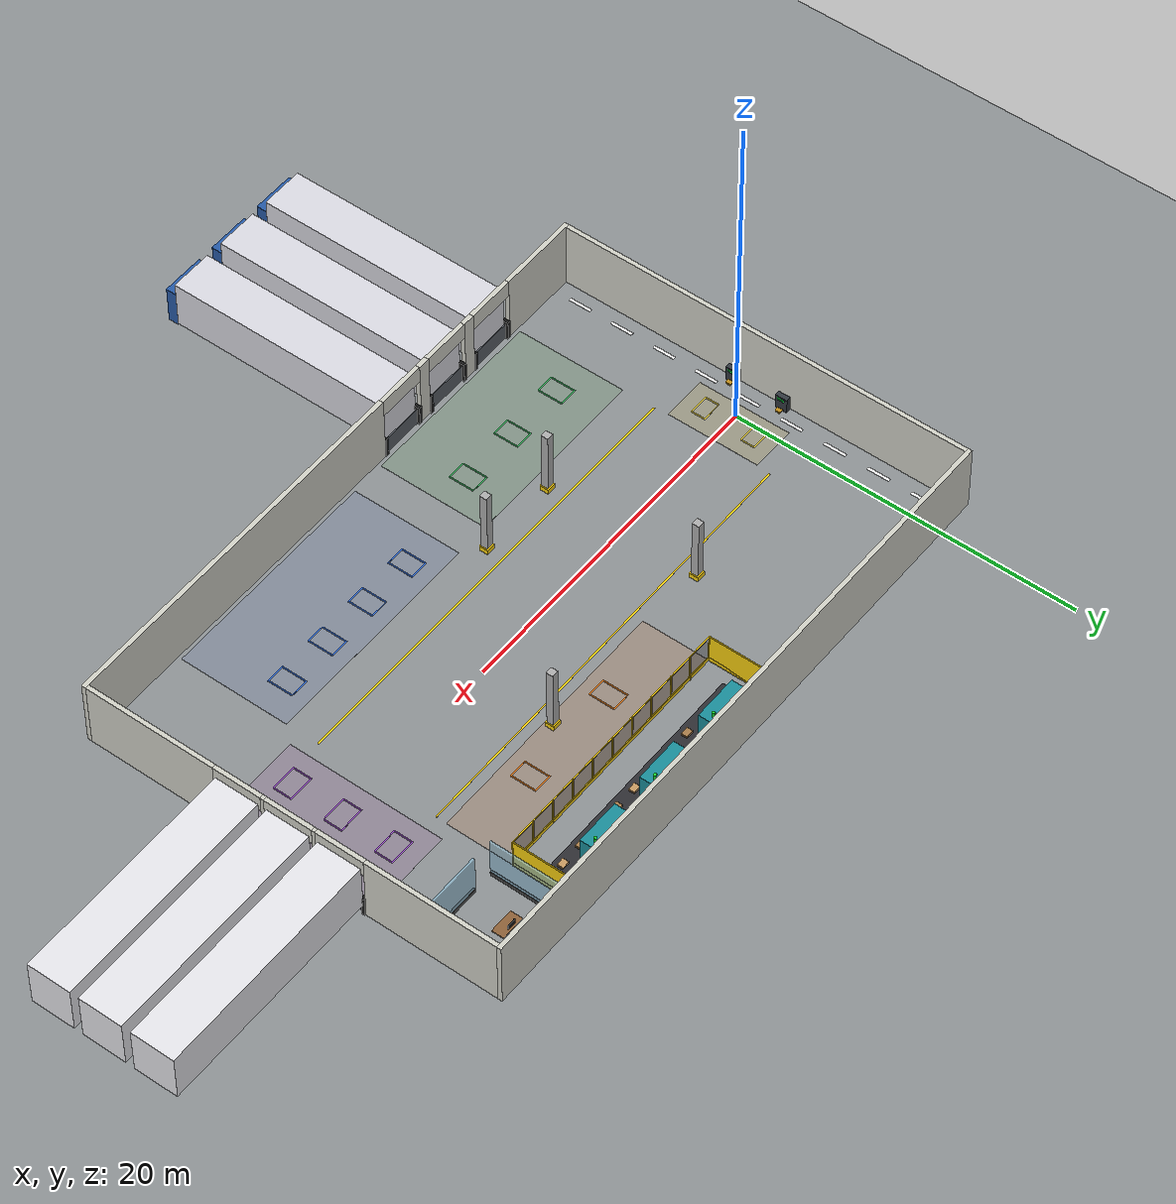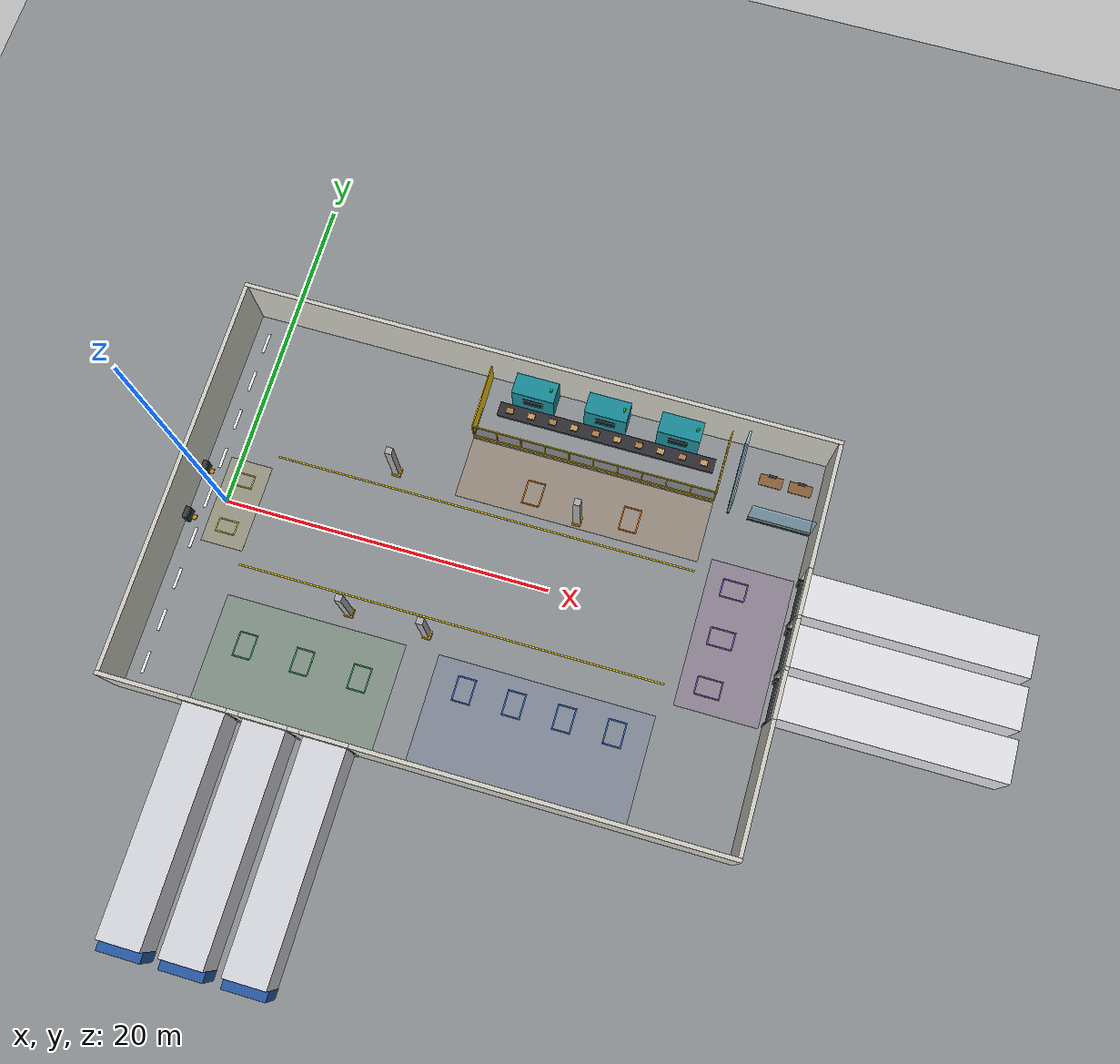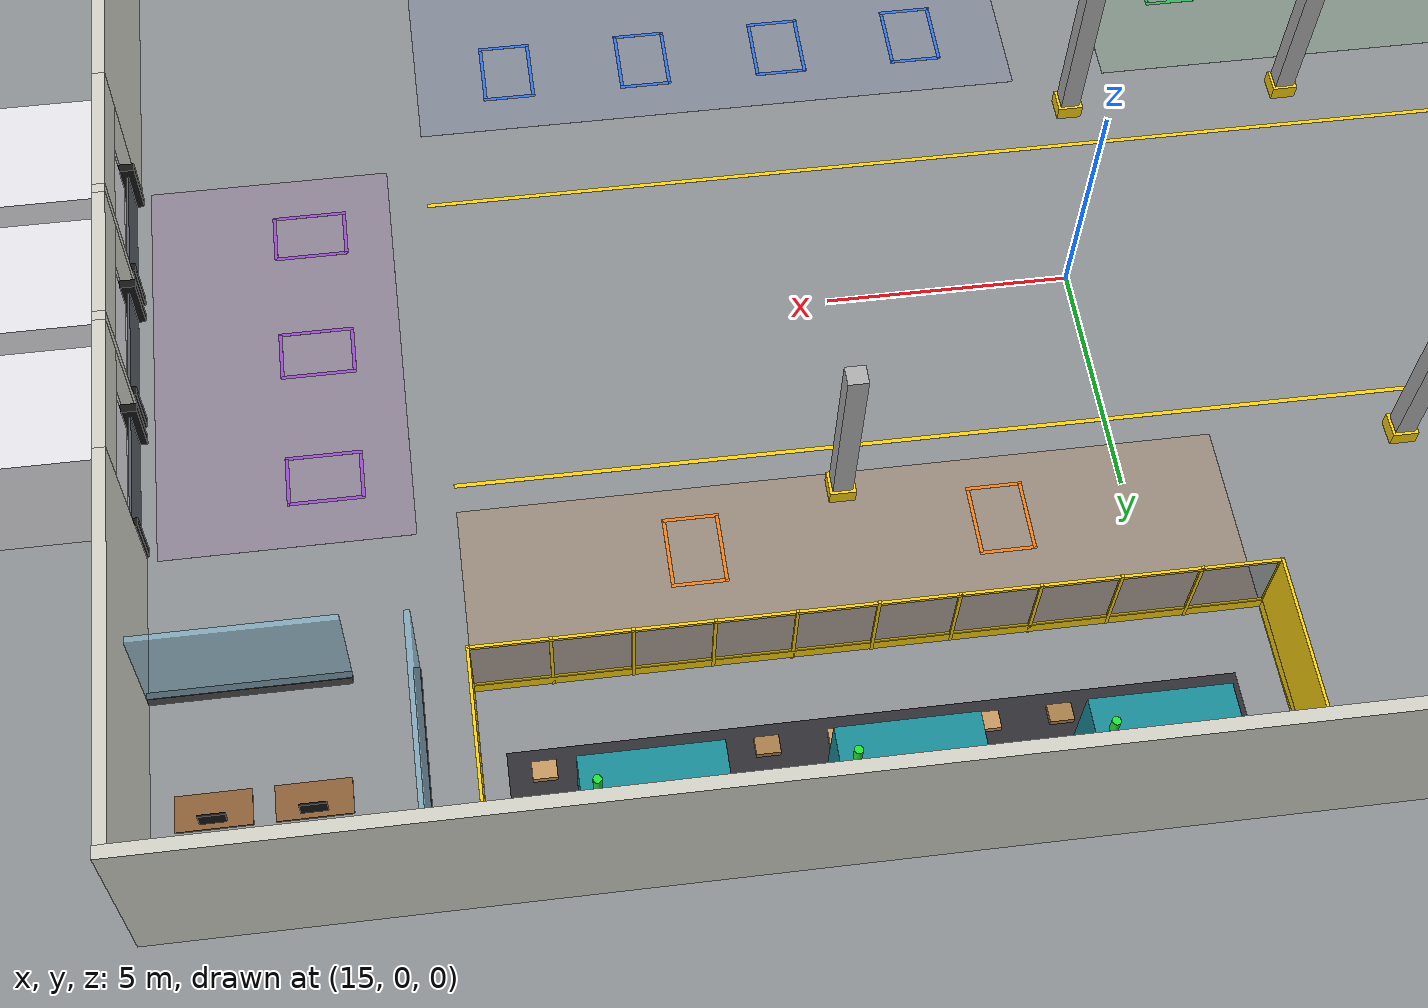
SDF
<sdf version="1.6">
 <world name="yektemak_factory">
  <gravity>0 0 -9.81</gravity>
  <plugin name="gazebo_ros_state" filename="libgazebo_ros_state.so">
   <ros><namespace>/gazebo</namespace></ros>
   <update_rate>20.0</update_rate>
  </plugin>
  <physics name="default_physics" type="ode">
   <max_step_size>0.001</max_step_size>
   <real_time_factor>1.0</real_time_factor>
   <real_time_update_rate>1000</real_time_update_rate>
  </physics>
  <scene>
   <ambient>0.6 0.6 0.6 1</ambient>
   <background>0.70 0.76 0.82 1</background>
   <shadows>true</shadows>
  </scene>
  <light type="directional" name="sun">
   <pose>0 0 20 0 0 0</pose>
   <diffuse>0.8 0.8 0.8 1</diffuse>
   <specular>0.2 0.2 0.2 1</specular>
   <direction>-0.35 0.25 -0.9</direction>
  </light>
  <model name="ground_plane">
   <static>true</static>
   <link name="link">
    <collision name="collision">
     <geometry><plane><normal>0 0 1</normal><size>120 120</size></plane></geometry>
     <surface><friction><ode><mu>1.0</mu><mu2>1.0</mu2></ode></friction></surface>
    </collision>
    <visual name="visual">
     <cast_shadows>false</cast_shadows>
     <geometry><plane><normal>0 0 1</normal><size>120 120</size></plane></geometry>
     <material>
      <ambient>0.44 0.46 0.46 1</ambient>
      <diffuse>0.55 0.57 0.58 1</diffuse>
      <specular>0.1 0.1 0.1 1</specular>
     </material>
    </visual>
   </link>
  </model>
  <model name="factory_building">
   <static>true</static>
   <link name="link">
    <collision name="b1_c">
     <pose>16 12.12 2 0 0 0</pose>
     <geometry><box><size>36.5 0.25 4</size></box></geometry>
    </collision>
    <visual name="b1_v">
     <pose>16 12.12 2 0 0 0</pose>
     <geometry><box><size>36.5 0.25 4</size></box></geometry>
     <material>
      <ambient>0.66 0.66 0.62 1</ambient>
      <diffuse>0.82 0.82 0.78 1</diffuse>
      <specular>0.1 0.1 0.1 1</specular>
     </material>
    </visual>
    <collision name="b2_c">
     <pose>-2.125 0 2 0 0 0</pose>
     <geometry><box><size>0.25 24 4</size></box></geometry>
    </collision>
    <visual name="b2_v">
     <pose>-2.125 0 2 0 0 0</pose>
     <geometry><box><size>0.25 24 4</size></box></geometry>
     <material>
      <ambient>0.66 0.66 0.62 1</ambient>
      <diffuse>0.82 0.82 0.78 1</diffuse>
      <specular>0.1 0.1 0.1 1</specular>
     </material>
    </visual>
    <collision name="b3_c">
     <pose>0.175 -12.12 2 0 0 0</pose>
     <geometry><box><size>4.85 0.25 4</size></box></geometry>
    </collision>
    <visual name="b3_v">
     <pose>0.175 -12.12 2 0 0 0</pose>
     <geometry><box><size>4.85 0.25 4</size></box></geometry>
     <material>
      <ambient>0.66 0.66 0.62 1</ambient>
      <diffuse>0.82 0.82 0.78 1</diffuse>
      <specular>0.1 0.1 0.1 1</specular>
     </material>
    </visual>
    <collision name="b4_c">
     <pose>5.75 -12.12 2 0 0 0</pose>
     <geometry><box><size>0.7 0.25 4</size></box></geometry>
    </collision>
    <visual name="b4_v">
     <pose>5.75 -12.12 2 0 0 0</pose>
     <geometry><box><size>0.7 0.25 4</size></box></geometry>
     <material>
      <ambient>0.66 0.66 0.62 1</ambient>
      <diffuse>0.82 0.82 0.78 1</diffuse>
      <specular>0.1 0.1 0.1 1</specular>
     </material>
    </visual>
    <collision name="b5_c">
     <pose>9.25 -12.12 2 0 0 0</pose>
     <geometry><box><size>0.7 0.25 4</size></box></geometry>
    </collision>
    <visual name="b5_v">
     <pose>9.25 -12.12 2 0 0 0</pose>
     <geometry><box><size>0.7 0.25 4</size></box></geometry>
     <material>
      <ambient>0.66 0.66 0.62 1</ambient>
      <diffuse>0.82 0.82 0.78 1</diffuse>
      <specular>0.1 0.1 0.1 1</specular>
     </material>
    </visual>
    <collision name="b6_c">
     <pose>23.32 -12.12 2 0 0 0</pose>
     <geometry><box><size>21.85 0.25 4</size></box></geometry>
    </collision>
    <visual name="b6_v">
     <pose>23.32 -12.12 2 0 0 0</pose>
     <geometry><box><size>21.85 0.25 4</size></box></geometry>
     <material>
      <ambient>0.66 0.66 0.62 1</ambient>
      <diffuse>0.82 0.82 0.78 1</diffuse>
      <specular>0.1 0.1 0.1 1</specular>
     </material>
    </visual>
    <collision name="b7_c">
     <pose>4 -12.12 3.5 0 0 0</pose>
     <geometry><box><size>2.8 0.25 1</size></box></geometry>
    </collision>
    <visual name="b7_v">
     <pose>4 -12.12 3.5 0 0 0</pose>
     <geometry><box><size>2.8 0.25 1</size></box></geometry>
     <material>
      <ambient>0.66 0.66 0.62 1</ambient>
      <diffuse>0.82 0.82 0.78 1</diffuse>
      <specular>0.1 0.1 0.1 1</specular>
     </material>
    </visual>
    <collision name="b8_c">
     <pose>4 -12.12 0.5 0 0 0</pose>
     <geometry><box><size>2.8 0.05 1</size></box></geometry>
    </collision>
    <visual name="b8_v">
     <pose>4 -12.12 0.5 0 0 0</pose>
     <geometry><box><size>2.8 0.05 1</size></box></geometry>
     <material>
      <ambient>0.28 0.30 0.32 1</ambient>
      <diffuse>0.35 0.37 0.4 1</diffuse>
      <specular>0.1 0.1 0.1 1</specular>
     </material>
    </visual>
    <collision name="b9_c">
     <pose>2.7 -12.12 0.6 0 0 0</pose>
     <geometry><box><size>0.18 0.35 1.2</size></box></geometry>
    </collision>
    <visual name="b9_v">
     <pose>2.7 -12.12 0.6 0 0 0</pose>
     <geometry><box><size>0.18 0.35 1.2</size></box></geometry>
     <material>
      <ambient>0.06 0.06 0.06 1</ambient>
      <diffuse>0.08 0.08 0.08 1</diffuse>
      <specular>0.1 0.1 0.1 1</specular>
     </material>
    </visual>
    <collision name="b10_c">
     <pose>5.3 -12.12 0.6 0 0 0</pose>
     <geometry><box><size>0.18 0.35 1.2</size></box></geometry>
    </collision>
    <visual name="b10_v">
     <pose>5.3 -12.12 0.6 0 0 0</pose>
     <geometry><box><size>0.18 0.35 1.2</size></box></geometry>
     <material>
      <ambient>0.06 0.06 0.06 1</ambient>
      <diffuse>0.08 0.08 0.08 1</diffuse>
      <specular>0.1 0.1 0.1 1</specular>
     </material>
    </visual>
    <collision name="b11_c">
     <pose>7.5 -12.12 3.5 0 0 0</pose>
     <geometry><box><size>2.8 0.25 1</size></box></geometry>
    </collision>
    <visual name="b11_v">
     <pose>7.5 -12.12 3.5 0 0 0</pose>
     <geometry><box><size>2.8 0.25 1</size></box></geometry>
     <material>
      <ambient>0.66 0.66 0.62 1</ambient>
      <diffuse>0.82 0.82 0.78 1</diffuse>
      <specular>0.1 0.1 0.1 1</specular>
     </material>
    </visual>
    <collision name="b12_c">
     <pose>7.5 -12.12 0.5 0 0 0</pose>
     <geometry><box><size>2.8 0.05 1</size></box></geometry>
    </collision>
    <visual name="b12_v">
     <pose>7.5 -12.12 0.5 0 0 0</pose>
     <geometry><box><size>2.8 0.05 1</size></box></geometry>
     <material>
      <ambient>0.28 0.30 0.32 1</ambient>
      <diffuse>0.35 0.37 0.4 1</diffuse>
      <specular>0.1 0.1 0.1 1</specular>
     </material>
    </visual>
    <collision name="b13_c">
     <pose>6.2 -12.12 0.6 0 0 0</pose>
     <geometry><box><size>0.18 0.35 1.2</size></box></geometry>
    </collision>
    <visual name="b13_v">
     <pose>6.2 -12.12 0.6 0 0 0</pose>
     <geometry><box><size>0.18 0.35 1.2</size></box></geometry>
     <material>
      <ambient>0.06 0.06 0.06 1</ambient>
      <diffuse>0.08 0.08 0.08 1</diffuse>
      <specular>0.1 0.1 0.1 1</specular>
     </material>
    </visual>
    <collision name="b14_c">
     <pose>8.8 -12.12 0.6 0 0 0</pose>
     <geometry><box><size>0.18 0.35 1.2</size></box></geometry>
    </collision>
    <visual name="b14_v">
     <pose>8.8 -12.12 0.6 0 0 0</pose>
     <geometry><box><size>0.18 0.35 1.2</size></box></geometry>
     <material>
      <ambient>0.06 0.06 0.06 1</ambient>
      <diffuse>0.08 0.08 0.08 1</diffuse>
      <specular>0.1 0.1 0.1 1</specular>
     </material>
    </visual>
    <collision name="b15_c">
     <pose>11 -12.12 3.5 0 0 0</pose>
     <geometry><box><size>2.8 0.25 1</size></box></geometry>
    </collision>
    <visual name="b15_v">
     <pose>11 -12.12 3.5 0 0 0</pose>
     <geometry><box><size>2.8 0.25 1</size></box></geometry>
     <material>
      <ambient>0.66 0.66 0.62 1</ambient>
      <diffuse>0.82 0.82 0.78 1</diffuse>
      <specular>0.1 0.1 0.1 1</specular>
     </material>
    </visual>
    <collision name="b16_c">
     <pose>11 -12.12 0.5 0 0 0</pose>
     <geometry><box><size>2.8 0.05 1</size></box></geometry>
    </collision>
    <visual name="b16_v">
     <pose>11 -12.12 0.5 0 0 0</pose>
     <geometry><box><size>2.8 0.05 1</size></box></geometry>
     <material>
      <ambient>0.28 0.30 0.32 1</ambient>
      <diffuse>0.35 0.37 0.4 1</diffuse>
      <specular>0.1 0.1 0.1 1</specular>
     </material>
    </visual>
    <collision name="b17_c">
     <pose>9.7 -12.12 0.6 0 0 0</pose>
     <geometry><box><size>0.18 0.35 1.2</size></box></geometry>
    </collision>
    <visual name="b17_v">
     <pose>9.7 -12.12 0.6 0 0 0</pose>
     <geometry><box><size>0.18 0.35 1.2</size></box></geometry>
     <material>
      <ambient>0.06 0.06 0.06 1</ambient>
      <diffuse>0.08 0.08 0.08 1</diffuse>
      <specular>0.1 0.1 0.1 1</specular>
     </material>
    </visual>
    <collision name="b18_c">
     <pose>12.3 -12.12 0.6 0 0 0</pose>
     <geometry><box><size>0.18 0.35 1.2</size></box></geometry>
    </collision>
    <visual name="b18_v">
     <pose>12.3 -12.12 0.6 0 0 0</pose>
     <geometry><box><size>0.18 0.35 1.2</size></box></geometry>
     <material>
      <ambient>0.06 0.06 0.06 1</ambient>
      <diffuse>0.08 0.08 0.08 1</diffuse>
      <specular>0.1 0.1 0.1 1</specular>
     </material>
    </visual>
    <collision name="b19_c">
     <pose>34.12 -8.2 2 0 0 0</pose>
     <geometry><box><size>0.25 7.6 4</size></box></geometry>
    </collision>
    <visual name="b19_v">
     <pose>34.12 -8.2 2 0 0 0</pose>
     <geometry><box><size>0.25 7.6 4</size></box></geometry>
     <material>
      <ambient>0.66 0.66 0.62 1</ambient>
      <diffuse>0.82 0.82 0.78 1</diffuse>
      <specular>0.1 0.1 0.1 1</specular>
     </material>
    </visual>
    <collision name="b20_c">
     <pose>34.12 -1.5 2 0 0 0</pose>
     <geometry><box><size>0.25 0.2 4</size></box></geometry>
    </collision>
    <visual name="b20_v">
     <pose>34.12 -1.5 2 0 0 0</pose>
     <geometry><box><size>0.25 0.2 4</size></box></geometry>
     <material>
      <ambient>0.66 0.66 0.62 1</ambient>
      <diffuse>0.82 0.82 0.78 1</diffuse>
      <specular>0.1 0.1 0.1 1</specular>
     </material>
    </visual>
    <collision name="b21_c">
     <pose>34.12 1.5 2 0 0 0</pose>
     <geometry><box><size>0.25 0.2 4</size></box></geometry>
    </collision>
    <visual name="b21_v">
     <pose>34.12 1.5 2 0 0 0</pose>
     <geometry><box><size>0.25 0.2 4</size></box></geometry>
     <material>
      <ambient>0.66 0.66 0.62 1</ambient>
      <diffuse>0.82 0.82 0.78 1</diffuse>
      <specular>0.1 0.1 0.1 1</specular>
     </material>
    </visual>
    <collision name="b22_c">
     <pose>34.12 8.2 2 0 0 0</pose>
     <geometry><box><size>0.25 7.6 4</size></box></geometry>
    </collision>
    <visual name="b22_v">
     <pose>34.12 8.2 2 0 0 0</pose>
     <geometry><box><size>0.25 7.6 4</size></box></geometry>
     <material>
      <ambient>0.66 0.66 0.62 1</ambient>
      <diffuse>0.82 0.82 0.78 1</diffuse>
      <specular>0.1 0.1 0.1 1</specular>
     </material>
    </visual>
    <collision name="b23_c">
     <pose>34.12 -3 3.5 0 0 0</pose>
     <geometry><box><size>0.25 2.8 1</size></box></geometry>
    </collision>
    <visual name="b23_v">
     <pose>34.12 -3 3.5 0 0 0</pose>
     <geometry><box><size>0.25 2.8 1</size></box></geometry>
     <material>
      <ambient>0.66 0.66 0.62 1</ambient>
      <diffuse>0.82 0.82 0.78 1</diffuse>
      <specular>0.1 0.1 0.1 1</specular>
     </material>
    </visual>
    <collision name="b24_c">
     <pose>34.12 -3 0.5 0 0 0</pose>
     <geometry><box><size>0.05 2.8 1</size></box></geometry>
    </collision>
    <visual name="b24_v">
     <pose>34.12 -3 0.5 0 0 0</pose>
     <geometry><box><size>0.05 2.8 1</size></box></geometry>
     <material>
      <ambient>0.28 0.30 0.32 1</ambient>
      <diffuse>0.35 0.37 0.4 1</diffuse>
      <specular>0.1 0.1 0.1 1</specular>
     </material>
    </visual>
    <collision name="b25_c">
     <pose>34.12 -4.3 0.6 0 0 0</pose>
     <geometry><box><size>0.35 0.18 1.2</size></box></geometry>
    </collision>
    <visual name="b25_v">
     <pose>34.12 -4.3 0.6 0 0 0</pose>
     <geometry><box><size>0.35 0.18 1.2</size></box></geometry>
     <material>
      <ambient>0.06 0.06 0.06 1</ambient>
      <diffuse>0.08 0.08 0.08 1</diffuse>
      <specular>0.1 0.1 0.1 1</specular>
     </material>
    </visual>
    <collision name="b26_c">
     <pose>34.12 -1.7 0.6 0 0 0</pose>
     <geometry><box><size>0.35 0.18 1.2</size></box></geometry>
    </collision>
    <visual name="b26_v">
     <pose>34.12 -1.7 0.6 0 0 0</pose>
     <geometry><box><size>0.35 0.18 1.2</size></box></geometry>
     <material>
      <ambient>0.06 0.06 0.06 1</ambient>
      <diffuse>0.08 0.08 0.08 1</diffuse>
      <specular>0.1 0.1 0.1 1</specular>
     </material>
    </visual>
    <collision name="b27_c">
     <pose>34.12 0 3.5 0 0 0</pose>
     <geometry><box><size>0.25 2.8 1</size></box></geometry>
    </collision>
    <visual name="b27_v">
     <pose>34.12 0 3.5 0 0 0</pose>
     <geometry><box><size>0.25 2.8 1</size></box></geometry>
     <material>
      <ambient>0.66 0.66 0.62 1</ambient>
      <diffuse>0.82 0.82 0.78 1</diffuse>
      <specular>0.1 0.1 0.1 1</specular>
     </material>
    </visual>
    <collision name="b28_c">
     <pose>34.12 0 0.5 0 0 0</pose>
     <geometry><box><size>0.05 2.8 1</size></box></geometry>
    </collision>
    <visual name="b28_v">
     <pose>34.12 0 0.5 0 0 0</pose>
     <geometry><box><size>0.05 2.8 1</size></box></geometry>
     <material>
      <ambient>0.28 0.30 0.32 1</ambient>
      <diffuse>0.35 0.37 0.4 1</diffuse>
      <specular>0.1 0.1 0.1 1</specular>
     </material>
    </visual>
    <collision name="b29_c">
     <pose>34.12 -1.3 0.6 0 0 0</pose>
     <geometry><box><size>0.35 0.18 1.2</size></box></geometry>
    </collision>
    <visual name="b29_v">
     <pose>34.12 -1.3 0.6 0 0 0</pose>
     <geometry><box><size>0.35 0.18 1.2</size></box></geometry>
     <material>
      <ambient>0.06 0.06 0.06 1</ambient>
      <diffuse>0.08 0.08 0.08 1</diffuse>
      <specular>0.1 0.1 0.1 1</specular>
     </material>
    </visual>
    <collision name="b30_c">
     <pose>34.12 1.3 0.6 0 0 0</pose>
     <geometry><box><size>0.35 0.18 1.2</size></box></geometry>
    </collision>
    <visual name="b30_v">
     <pose>34.12 1.3 0.6 0 0 0</pose>
     <geometry><box><size>0.35 0.18 1.2</size></box></geometry>
     <material>
      <ambient>0.06 0.06 0.06 1</ambient>
      <diffuse>0.08 0.08 0.08 1</diffuse>
      <specular>0.1 0.1 0.1 1</specular>
     </material>
    </visual>
    <collision name="b31_c">
     <pose>34.12 3 3.5 0 0 0</pose>
     <geometry><box><size>0.25 2.8 1</size></box></geometry>
    </collision>
    <visual name="b31_v">
     <pose>34.12 3 3.5 0 0 0</pose>
     <geometry><box><size>0.25 2.8 1</size></box></geometry>
     <material>
      <ambient>0.66 0.66 0.62 1</ambient>
      <diffuse>0.82 0.82 0.78 1</diffuse>
      <specular>0.1 0.1 0.1 1</specular>
     </material>
    </visual>
    <collision name="b32_c">
     <pose>34.12 3 0.5 0 0 0</pose>
     <geometry><box><size>0.05 2.8 1</size></box></geometry>
    </collision>
    <visual name="b32_v">
     <pose>34.12 3 0.5 0 0 0</pose>
     <geometry><box><size>0.05 2.8 1</size></box></geometry>
     <material>
      <ambient>0.28 0.30 0.32 1</ambient>
      <diffuse>0.35 0.37 0.4 1</diffuse>
      <specular>0.1 0.1 0.1 1</specular>
     </material>
    </visual>
    <collision name="b33_c">
     <pose>34.12 1.7 0.6 0 0 0</pose>
     <geometry><box><size>0.35 0.18 1.2</size></box></geometry>
    </collision>
    <visual name="b33_v">
     <pose>34.12 1.7 0.6 0 0 0</pose>
     <geometry><box><size>0.35 0.18 1.2</size></box></geometry>
     <material>
      <ambient>0.06 0.06 0.06 1</ambient>
      <diffuse>0.08 0.08 0.08 1</diffuse>
      <specular>0.1 0.1 0.1 1</specular>
     </material>
    </visual>
    <collision name="b34_c">
     <pose>34.12 4.3 0.6 0 0 0</pose>
     <geometry><box><size>0.35 0.18 1.2</size></box></geometry>
    </collision>
    <visual name="b34_v">
     <pose>34.12 4.3 0.6 0 0 0</pose>
     <geometry><box><size>0.35 0.18 1.2</size></box></geometry>
     <material>
      <ambient>0.06 0.06 0.06 1</ambient>
      <diffuse>0.08 0.08 0.08 1</diffuse>
      <specular>0.1 0.1 0.1 1</specular>
     </material>
    </visual>
    <collision name="b35_c">
     <pose>9.25 4.5 2 0 0 0</pose>
     <geometry><box><size>0.4 0.4 4</size></box></geometry>
    </collision>
    <visual name="b35_v">
     <pose>9.25 4.5 2 0 0 0</pose>
     <geometry><box><size>0.4 0.4 4</size></box></geometry>
     <material>
      <ambient>0.54 0.54 0.54 1</ambient>
      <diffuse>0.68 0.68 0.68 1</diffuse>
      <specular>0.1 0.1 0.1 1</specular>
     </material>
    </visual>
    <collision name="b36_c">
     <pose>9.25 4.5 0.15 0 0 0</pose>
     <geometry><box><size>0.52 0.52 0.3</size></box></geometry>
    </collision>
    <visual name="b36_v">
     <pose>9.25 4.5 0.15 0 0 0</pose>
     <geometry><box><size>0.52 0.52 0.3</size></box></geometry>
     <material>
      <ambient>0.78 0.66 0.04 1</ambient>
      <diffuse>0.98 0.82 0.05 1</diffuse>
      <specular>0.1 0.1 0.1 1</specular>
     </material>
    </visual>
    <collision name="b37_c">
     <pose>9.25 -4.5 2 0 0 0</pose>
     <geometry><box><size>0.4 0.4 4</size></box></geometry>
    </collision>
    <visual name="b37_v">
     <pose>9.25 -4.5 2 0 0 0</pose>
     <geometry><box><size>0.4 0.4 4</size></box></geometry>
     <material>
      <ambient>0.54 0.54 0.54 1</ambient>
      <diffuse>0.68 0.68 0.68 1</diffuse>
      <specular>0.1 0.1 0.1 1</specular>
     </material>
    </visual>
    <collision name="b38_c">
     <pose>9.25 -4.5 0.15 0 0 0</pose>
     <geometry><box><size>0.52 0.52 0.3</size></box></geometry>
    </collision>
    <visual name="b38_v">
     <pose>9.25 -4.5 0.15 0 0 0</pose>
     <geometry><box><size>0.52 0.52 0.3</size></box></geometry>
     <material>
      <ambient>0.78 0.66 0.04 1</ambient>
      <diffuse>0.98 0.82 0.05 1</diffuse>
      <specular>0.1 0.1 0.1 1</specular>
     </material>
    </visual>
    <collision name="b39_c">
     <pose>20.5 4.5 2 0 0 0</pose>
     <geometry><box><size>0.4 0.4 4</size></box></geometry>
    </collision>
    <visual name="b39_v">
     <pose>20.5 4.5 2 0 0 0</pose>
     <geometry><box><size>0.4 0.4 4</size></box></geometry>
     <material>
      <ambient>0.54 0.54 0.54 1</ambient>
      <diffuse>0.68 0.68 0.68 1</diffuse>
      <specular>0.1 0.1 0.1 1</specular>
     </material>
    </visual>
    <collision name="b40_c">
     <pose>20.5 4.5 0.15 0 0 0</pose>
     <geometry><box><size>0.52 0.52 0.3</size></box></geometry>
    </collision>
    <visual name="b40_v">
     <pose>20.5 4.5 0.15 0 0 0</pose>
     <geometry><box><size>0.52 0.52 0.3</size></box></geometry>
     <material>
      <ambient>0.78 0.66 0.04 1</ambient>
      <diffuse>0.98 0.82 0.05 1</diffuse>
      <specular>0.1 0.1 0.1 1</specular>
     </material>
    </visual>
    <collision name="b41_c">
     <pose>14 -4.5 2 0 0 0</pose>
     <geometry><box><size>0.4 0.4 4</size></box></geometry>
    </collision>
    <visual name="b41_v">
     <pose>14 -4.5 2 0 0 0</pose>
     <geometry><box><size>0.4 0.4 4</size></box></geometry>
     <material>
      <ambient>0.54 0.54 0.54 1</ambient>
      <diffuse>0.68 0.68 0.68 1</diffuse>
      <specular>0.1 0.1 0.1 1</specular>
     </material>
    </visual>
    <collision name="b42_c">
     <pose>14 -4.5 0.15 0 0 0</pose>
     <geometry><box><size>0.52 0.52 0.3</size></box></geometry>
    </collision>
    <visual name="b42_v">
     <pose>14 -4.5 0.15 0 0 0</pose>
     <geometry><box><size>0.52 0.52 0.3</size></box></geometry>
     <material>
      <ambient>0.78 0.66 0.04 1</ambient>
      <diffuse>0.98 0.82 0.05 1</diffuse>
      <specular>0.1 0.1 0.1 1</specular>
     </material>
    </visual>
    <collision name="b43_c">
     <pose>32.1 7.5 1.25 0 0 0</pose>
     <geometry><box><size>3.8 0.12 2.5</size></box></geometry>
    </collision>
    <visual name="b43_v">
     <pose>32.1 7.5 1.25 0 0 0</pose>
     <geometry><box><size>3.8 0.12 2.5</size></box></geometry>
     <material>
      <ambient>0.44 0.60 0.68 1</ambient>
      <diffuse>0.55 0.75 0.85 1</diffuse>
      <specular>0.1 0.1 0.1 1</specular>
     </material>
     <transparency>0.35</transparency>
    </visual>
    <collision name="b44_c">
     <pose>29 9.75 1.25 0 0 0</pose>
     <geometry><box><size>0.12 4.5 2.5</size></box></geometry>
    </collision>
    <visual name="b44_v">
     <pose>29 9.75 1.25 0 0 0</pose>
     <geometry><box><size>0.12 4.5 2.5</size></box></geometry>
     <material>
      <ambient>0.44 0.60 0.68 1</ambient>
      <diffuse>0.55 0.75 0.85 1</diffuse>
      <specular>0.1 0.1 0.1 1</specular>
     </material>
     <transparency>0.35</transparency>
    </visual>
    <collision name="b45_c">
     <pose>32.1 7.5 0.12 0 0 0</pose>
     <geometry><box><size>3.8 0.14 0.24</size></box></geometry>
    </collision>
    <visual name="b45_v">
     <pose>32.1 7.5 0.12 0 0 0</pose>
     <geometry><box><size>3.8 0.14 0.24</size></box></geometry>
     <material>
      <ambient>0.24 0.24 0.24 1</ambient>
      <diffuse>0.3 0.3 0.3 1</diffuse>
      <specular>0.1 0.1 0.1 1</specular>
     </material>
    </visual>
    <collision name="b46_c">
     <pose>29 9.75 0.12 0 0 0</pose>
     <geometry><box><size>0.14 4.5 0.24</size></box></geometry>
    </collision>
    <visual name="b46_v">
     <pose>29 9.75 0.12 0 0 0</pose>
     <geometry><box><size>0.14 4.5 0.24</size></box></geometry>
     <material>
      <ambient>0.24 0.24 0.24 1</ambient>
      <diffuse>0.3 0.3 0.3 1</diffuse>
      <specular>0.1 0.1 0.1 1</specular>
     </material>
    </visual>
    <collision name="b47_c">
     <pose>31 10 0.38 0 0 0</pose>
     <geometry><box><size>1.4 0.7 0.04</size></box></geometry>
    </collision>
    <visual name="b47_v">
     <pose>31 10 0.38 0 0 0</pose>
     <geometry><box><size>1.4 0.7 0.04</size></box></geometry>
     <material>
      <ambient>0.44 0.30 0.18 1</ambient>
      <diffuse>0.55 0.38 0.22 1</diffuse>
      <specular>0.1 0.1 0.1 1</specular>
     </material>
    </visual>
    <visual name="b48_v">
     <pose>31 10.25 0.62 0 0 0</pose>
     <cast_shadows>false</cast_shadows>
     <geometry><box><size>0.5 0.04 0.32</size></box></geometry>
     <material>
      <ambient>0.06 0.06 0.06 1</ambient>
      <diffuse>0.08 0.08 0.08 1</diffuse>
      <specular>0.1 0.1 0.1 1</specular>
     </material>
    </visual>
    <collision name="b49_c">
     <pose>32.8 10 0.38 0 0 0</pose>
     <geometry><box><size>1.4 0.7 0.04</size></box></geometry>
    </collision>
    <visual name="b49_v">
     <pose>32.8 10 0.38 0 0 0</pose>
     <geometry><box><size>1.4 0.7 0.04</size></box></geometry>
     <material>
      <ambient>0.44 0.30 0.18 1</ambient>
      <diffuse>0.55 0.38 0.22 1</diffuse>
      <specular>0.1 0.1 0.1 1</specular>
     </material>
    </visual>
    <visual name="b50_v">
     <pose>32.8 10.25 0.62 0 0 0</pose>
     <cast_shadows>false</cast_shadows>
     <geometry><box><size>0.5 0.04 0.32</size></box></geometry>
     <material>
      <ambient>0.06 0.06 0.06 1</ambient>
      <diffuse>0.08 0.08 0.08 1</diffuse>
      <specular>0.1 0.1 0.1 1</specular>
     </material>
    </visual>
   </link>
  </model>
  <model name="trucks">
   <static>true</static>
   <link name="link">
    <visual name="b51_v">
     <pose>4 -18.75 2 0 0 0</pose>
     <cast_shadows>false</cast_shadows>
     <geometry><box><size>2.5 13 2.8</size></box></geometry>
     <material>
      <ambient>0.68 0.68 0.70 1</ambient>
      <diffuse>0.85 0.85 0.88 1</diffuse>
      <specular>0.1 0.1 0.1 1</specular>
     </material>
    </visual>
    <visual name="b52_v">
     <pose>4 -25.55 1.6 0 0 0</pose>
     <cast_shadows>false</cast_shadows>
     <geometry><box><size>2.5 0.6 2.2</size></box></geometry>
     <material>
      <ambient>0.12 0.28 0.52 1</ambient>
      <diffuse>0.15 0.35 0.65 1</diffuse>
      <specular>0.1 0.1 0.1 1</specular>
     </material>
    </visual>
    <visual name="b53_v">
     <pose>7.5 -18.75 2 0 0 0</pose>
     <cast_shadows>false</cast_shadows>
     <geometry><box><size>2.5 13 2.8</size></box></geometry>
     <material>
      <ambient>0.68 0.68 0.70 1</ambient>
      <diffuse>0.85 0.85 0.88 1</diffuse>
      <specular>0.1 0.1 0.1 1</specular>
     </material>
    </visual>
    <visual name="b54_v">
     <pose>7.5 -25.55 1.6 0 0 0</pose>
     <cast_shadows>false</cast_shadows>
     <geometry><box><size>2.5 0.6 2.2</size></box></geometry>
     <material>
      <ambient>0.12 0.28 0.52 1</ambient>
      <diffuse>0.15 0.35 0.65 1</diffuse>
      <specular>0.1 0.1 0.1 1</specular>
     </material>
    </visual>
    <visual name="b55_v">
     <pose>11 -18.75 2 0 0 0</pose>
     <cast_shadows>false</cast_shadows>
     <geometry><box><size>2.5 13 2.8</size></box></geometry>
     <material>
      <ambient>0.68 0.68 0.70 1</ambient>
      <diffuse>0.85 0.85 0.88 1</diffuse>
      <specular>0.1 0.1 0.1 1</specular>
     </material>
    </visual>
    <visual name="b56_v">
     <pose>11 -25.55 1.6 0 0 0</pose>
     <cast_shadows>false</cast_shadows>
     <geometry><box><size>2.5 0.6 2.2</size></box></geometry>
     <material>
      <ambient>0.12 0.28 0.52 1</ambient>
      <diffuse>0.15 0.35 0.65 1</diffuse>
      <specular>0.1 0.1 0.1 1</specular>
     </material>
    </visual>
    <visual name="b57_v">
     <pose>40.75 -3 2 0 0 0</pose>
     <cast_shadows>false</cast_shadows>
     <geometry><box><size>13 2.5 2.8</size></box></geometry>
     <material>
      <ambient>0.72 0.72 0.74 1</ambient>
      <diffuse>0.9 0.9 0.92 1</diffuse>
      <specular>0.1 0.1 0.1 1</specular>
     </material>
    </visual>
    <visual name="b58_v">
     <pose>40.75 0 2 0 0 0</pose>
     <cast_shadows>false</cast_shadows>
     <geometry><box><size>13 2.5 2.8</size></box></geometry>
     <material>
      <ambient>0.72 0.72 0.74 1</ambient>
      <diffuse>0.9 0.9 0.92 1</diffuse>
      <specular>0.1 0.1 0.1 1</specular>
     </material>
    </visual>
    <visual name="b59_v">
     <pose>40.75 3 2 0 0 0</pose>
     <cast_shadows>false</cast_shadows>
     <geometry><box><size>13 2.5 2.8</size></box></geometry>
     <material>
      <ambient>0.72 0.72 0.74 1</ambient>
      <diffuse>0.9 0.9 0.92 1</diffuse>
      <specular>0.1 0.1 0.1 1</specular>
     </material>
    </visual>
   </link>
  </model>
  <model name="production_line">
   <static>true</static>
   <link name="link">
    <collision name="b60_c">
     <pose>20.75 10 0.42 0 0 0</pose>
     <geometry><box><size>13.5 0.9 0.08</size></box></geometry>
    </collision>
    <visual name="b60_v">
     <pose>20.75 10 0.42 0 0 0</pose>
     <geometry><box><size>13.5 0.9 0.08</size></box></geometry>
     <material>
      <ambient>0.14 0.14 0.16 1</ambient>
      <diffuse>0.18 0.18 0.2 1</diffuse>
      <specular>0.1 0.1 0.1 1</specular>
     </material>
    </visual>
    <collision name="b61_c">
     <pose>20.75 10 0.2 0 0 0</pose>
     <geometry><box><size>13.5 0.7 0.36</size></box></geometry>
    </collision>
    <visual name="b61_v">
     <pose>20.75 10 0.2 0 0 0</pose>
     <geometry><box><size>13.5 0.7 0.36</size></box></geometry>
     <material>
      <ambient>0.36 0.38 0.40 1</ambient>
      <diffuse>0.45 0.47 0.5 1</diffuse>
      <specular>0.1 0.1 0.1 1</specular>
     </material>
    </visual>
    <visual name="b62_v">
     <pose>14.7 10 0.52 0 0 0</pose>
     <cast_shadows>false</cast_shadows>
     <geometry><box><size>0.45 0.35 0.12</size></box></geometry>
     <material>
      <ambient>0.53 0.39 0.23 1</ambient>
      <diffuse>0.66 0.49 0.29 1</diffuse>
      <specular>0.1 0.1 0.1 1</specular>
     </material>
    </visual>
    <visual name="b63_v">
     <pose>16.05 10 0.52 0 0 0</pose>
     <cast_shadows>false</cast_shadows>
     <geometry><box><size>0.45 0.35 0.12</size></box></geometry>
     <material>
      <ambient>0.62 0.48 0.30 1</ambient>
      <diffuse>0.78 0.6 0.38 1</diffuse>
      <specular>0.1 0.1 0.1 1</specular>
     </material>
    </visual>
    <visual name="b64_v">
     <pose>17.4 10 0.52 0 0 0</pose>
     <cast_shadows>false</cast_shadows>
     <geometry><box><size>0.45 0.35 0.12</size></box></geometry>
     <material>
      <ambient>0.53 0.39 0.23 1</ambient>
      <diffuse>0.66 0.49 0.29 1</diffuse>
      <specular>0.1 0.1 0.1 1</specular>
     </material>
    </visual>
    <visual name="b65_v">
     <pose>18.75 10 0.52 0 0 0</pose>
     <cast_shadows>false</cast_shadows>
     <geometry><box><size>0.45 0.35 0.12</size></box></geometry>
     <material>
      <ambient>0.62 0.48 0.30 1</ambient>
      <diffuse>0.78 0.6 0.38 1</diffuse>
      <specular>0.1 0.1 0.1 1</specular>
     </material>
    </visual>
    <visual name="b66_v">
     <pose>20.1 10 0.52 0 0 0</pose>
     <cast_shadows>false</cast_shadows>
     <geometry><box><size>0.45 0.35 0.12</size></box></geometry>
     <material>
      <ambient>0.53 0.39 0.23 1</ambient>
      <diffuse>0.66 0.49 0.29 1</diffuse>
      <specular>0.1 0.1 0.1 1</specular>
     </material>
    </visual>
    <visual name="b67_v">
     <pose>21.45 10 0.52 0 0 0</pose>
     <cast_shadows>false</cast_shadows>
     <geometry><box><size>0.45 0.35 0.12</size></box></geometry>
     <material>
      <ambient>0.62 0.48 0.30 1</ambient>
      <diffuse>0.78 0.6 0.38 1</diffuse>
      <specular>0.1 0.1 0.1 1</specular>
     </material>
    </visual>
    <visual name="b68_v">
     <pose>22.8 10 0.52 0 0 0</pose>
     <cast_shadows>false</cast_shadows>
     <geometry><box><size>0.45 0.35 0.12</size></box></geometry>
     <material>
      <ambient>0.53 0.39 0.23 1</ambient>
      <diffuse>0.66 0.49 0.29 1</diffuse>
      <specular>0.1 0.1 0.1 1</specular>
     </material>
    </visual>
    <visual name="b69_v">
     <pose>24.15 10 0.52 0 0 0</pose>
     <cast_shadows>false</cast_shadows>
     <geometry><box><size>0.45 0.35 0.12</size></box></geometry>
     <material>
      <ambient>0.62 0.48 0.30 1</ambient>
      <diffuse>0.78 0.6 0.38 1</diffuse>
      <specular>0.1 0.1 0.1 1</specular>
     </material>
    </visual>
    <visual name="b70_v">
     <pose>25.5 10 0.52 0 0 0</pose>
     <cast_shadows>false</cast_shadows>
     <geometry><box><size>0.45 0.35 0.12</size></box></geometry>
     <material>
      <ambient>0.53 0.39 0.23 1</ambient>
      <diffuse>0.66 0.49 0.29 1</diffuse>
      <specular>0.1 0.1 0.1 1</specular>
     </material>
    </visual>
    <visual name="b71_v">
     <pose>26.85 10 0.52 0 0 0</pose>
     <cast_shadows>false</cast_shadows>
     <geometry><box><size>0.45 0.35 0.12</size></box></geometry>
     <material>
      <ambient>0.62 0.48 0.30 1</ambient>
      <diffuse>0.78 0.6 0.38 1</diffuse>
      <specular>0.1 0.1 0.1 1</specular>
     </material>
    </visual>
    <collision name="b72_c">
     <pose>16 11.2 1.1 0 0 0</pose>
     <geometry><box><size>2.6 1.3 2.2</size></box></geometry>
    </collision>
    <visual name="b72_v">
     <pose>16 11.2 1.1 0 0 0</pose>
     <geometry><box><size>2.6 1.3 2.2</size></box></geometry>
     <material>
      <ambient>0.08 0.44 0.48 1</ambient>
      <diffuse>0.1 0.55 0.6 1</diffuse>
      <specular>0.1 0.1 0.1 1</specular>
     </material>
    </visual>
    <visual name="b73_v">
     <pose>16 10.52 1.3 0 0 0</pose>
     <cast_shadows>false</cast_shadows>
     <geometry><box><size>1.2 0.06 0.6</size></box></geometry>
     <material>
      <ambient>0.04 0.06 0.08 1</ambient>
      <diffuse>0.05 0.08 0.1 1</diffuse>
      <specular>0.1 0.1 0.1 1</specular>
     </material>
    </visual>
    <visual name="c74_v">
     <pose>17 11.2 2.45 0 0 0</pose>
     <geometry><cylinder><radius>0.08</radius><length>0.3</length></cylinder></geometry>
     <material>
      <ambient>0.08 0.72 0.16 1</ambient>
      <diffuse>0.1 0.9 0.2 1</diffuse>
      <specular>0.1 0.1 0.1 1</specular>
      <emissive>0.1 0.9 0.2 1</emissive>
     </material>
    </visual>
    <collision name="b75_c">
     <pose>20.5 11.2 1.1 0 0 0</pose>
     <geometry><box><size>2.6 1.3 2.2</size></box></geometry>
    </collision>
    <visual name="b75_v">
     <pose>20.5 11.2 1.1 0 0 0</pose>
     <geometry><box><size>2.6 1.3 2.2</size></box></geometry>
     <material>
      <ambient>0.08 0.44 0.48 1</ambient>
      <diffuse>0.1 0.55 0.6 1</diffuse>
      <specular>0.1 0.1 0.1 1</specular>
     </material>
    </visual>
    <visual name="b76_v">
     <pose>20.5 10.52 1.3 0 0 0</pose>
     <cast_shadows>false</cast_shadows>
     <geometry><box><size>1.2 0.06 0.6</size></box></geometry>
     <material>
      <ambient>0.04 0.06 0.08 1</ambient>
      <diffuse>0.05 0.08 0.1 1</diffuse>
      <specular>0.1 0.1 0.1 1</specular>
     </material>
    </visual>
    <visual name="c77_v">
     <pose>21.5 11.2 2.45 0 0 0</pose>
     <geometry><cylinder><radius>0.08</radius><length>0.3</length></cylinder></geometry>
     <material>
      <ambient>0.08 0.72 0.16 1</ambient>
      <diffuse>0.1 0.9 0.2 1</diffuse>
      <specular>0.1 0.1 0.1 1</specular>
      <emissive>0.1 0.9 0.2 1</emissive>
     </material>
    </visual>
    <collision name="b78_c">
     <pose>25 11.2 1.1 0 0 0</pose>
     <geometry><box><size>2.6 1.3 2.2</size></box></geometry>
    </collision>
    <visual name="b78_v">
     <pose>25 11.2 1.1 0 0 0</pose>
     <geometry><box><size>2.6 1.3 2.2</size></box></geometry>
     <material>
      <ambient>0.08 0.44 0.48 1</ambient>
      <diffuse>0.1 0.55 0.6 1</diffuse>
      <specular>0.1 0.1 0.1 1</specular>
     </material>
    </visual>
    <visual name="b79_v">
     <pose>25 10.52 1.3 0 0 0</pose>
     <cast_shadows>false</cast_shadows>
     <geometry><box><size>1.2 0.06 0.6</size></box></geometry>
     <material>
      <ambient>0.04 0.06 0.08 1</ambient>
      <diffuse>0.05 0.08 0.1 1</diffuse>
      <specular>0.1 0.1 0.1 1</specular>
     </material>
    </visual>
    <visual name="c80_v">
     <pose>26 11.2 2.45 0 0 0</pose>
     <geometry><cylinder><radius>0.08</radius><length>0.3</length></cylinder></geometry>
     <material>
      <ambient>0.08 0.72 0.16 1</ambient>
      <diffuse>0.1 0.9 0.2 1</diffuse>
      <specular>0.1 0.1 0.1 1</specular>
      <emissive>0.1 0.9 0.2 1</emissive>
     </material>
    </visual>
    <collision name="b81_c">
     <pose>20.5 8 0.15 0 0 0</pose>
     <geometry><box><size>15 0.06 0.24</size></box></geometry>
    </collision>
    <visual name="b81_v">
     <pose>20.5 8 0.15 0 0 0</pose>
     <geometry><box><size>15 0.06 0.24</size></box></geometry>
     <material>
      <ambient>0.78 0.66 0.04 1</ambient>
      <diffuse>0.98 0.82 0.05 1</diffuse>
      <specular>0.1 0.1 0.1 1</specular>
     </material>
    </visual>
    <collision name="b82_c">
     <pose>20.5 8 1 0 0 0</pose>
     <geometry><box><size>15 0.02 1.5</size></box></geometry>
    </collision>
    <visual name="b82_v">
     <pose>20.5 8 1 0 0 0</pose>
     <geometry><box><size>15 0.02 1.5</size></box></geometry>
     <material>
      <ambient>0.24 0.24 0.24 1</ambient>
      <diffuse>0.3 0.3 0.3 1</diffuse>
      <specular>0.1 0.1 0.1 1</specular>
     </material>
     <transparency>0.6</transparency>
    </visual>
    <collision name="b83_c">
     <pose>20.5 8 1.75 0 0 0</pose>
     <geometry><box><size>15 0.06 0.06</size></box></geometry>
    </collision>
    <visual name="b83_v">
     <pose>20.5 8 1.75 0 0 0</pose>
     <geometry><box><size>15 0.06 0.06</size></box></geometry>
     <material>
      <ambient>0.78 0.66 0.04 1</ambient>
      <diffuse>0.98 0.82 0.05 1</diffuse>
      <specular>0.1 0.1 0.1 1</specular>
     </material>
    </visual>
    <collision name="b84_c">
     <pose>13 8 0.9 0 0 0</pose>
     <geometry><box><size>0.06 0.06 1.8</size></box></geometry>
    </collision>
    <visual name="b84_v">
     <pose>13 8 0.9 0 0 0</pose>
     <geometry><box><size>0.06 0.06 1.8</size></box></geometry>
     <material>
      <ambient>0.78 0.66 0.04 1</ambient>
      <diffuse>0.98 0.82 0.05 1</diffuse>
      <specular>0.1 0.1 0.1 1</specular>
     </material>
    </visual>
    <collision name="b85_c">
     <pose>14.5 8 0.9 0 0 0</pose>
     <geometry><box><size>0.06 0.06 1.8</size></box></geometry>
    </collision>
    <visual name="b85_v">
     <pose>14.5 8 0.9 0 0 0</pose>
     <geometry><box><size>0.06 0.06 1.8</size></box></geometry>
     <material>
      <ambient>0.78 0.66 0.04 1</ambient>
      <diffuse>0.98 0.82 0.05 1</diffuse>
      <specular>0.1 0.1 0.1 1</specular>
     </material>
    </visual>
    <collision name="b86_c">
     <pose>16 8 0.9 0 0 0</pose>
     <geometry><box><size>0.06 0.06 1.8</size></box></geometry>
    </collision>
    <visual name="b86_v">
     <pose>16 8 0.9 0 0 0</pose>
     <geometry><box><size>0.06 0.06 1.8</size></box></geometry>
     <material>
      <ambient>0.78 0.66 0.04 1</ambient>
      <diffuse>0.98 0.82 0.05 1</diffuse>
      <specular>0.1 0.1 0.1 1</specular>
     </material>
    </visual>
    <collision name="b87_c">
     <pose>17.5 8 0.9 0 0 0</pose>
     <geometry><box><size>0.06 0.06 1.8</size></box></geometry>
    </collision>
    <visual name="b87_v">
     <pose>17.5 8 0.9 0 0 0</pose>
     <geometry><box><size>0.06 0.06 1.8</size></box></geometry>
     <material>
      <ambient>0.78 0.66 0.04 1</ambient>
      <diffuse>0.98 0.82 0.05 1</diffuse>
      <specular>0.1 0.1 0.1 1</specular>
     </material>
    </visual>
    <collision name="b88_c">
     <pose>19 8 0.9 0 0 0</pose>
     <geometry><box><size>0.06 0.06 1.8</size></box></geometry>
    </collision>
    <visual name="b88_v">
     <pose>19 8 0.9 0 0 0</pose>
     <geometry><box><size>0.06 0.06 1.8</size></box></geometry>
     <material>
      <ambient>0.78 0.66 0.04 1</ambient>
      <diffuse>0.98 0.82 0.05 1</diffuse>
      <specular>0.1 0.1 0.1 1</specular>
     </material>
    </visual>
    <collision name="b89_c">
     <pose>20.5 8 0.9 0 0 0</pose>
     <geometry><box><size>0.06 0.06 1.8</size></box></geometry>
    </collision>
    <visual name="b89_v">
     <pose>20.5 8 0.9 0 0 0</pose>
     <geometry><box><size>0.06 0.06 1.8</size></box></geometry>
     <material>
      <ambient>0.78 0.66 0.04 1</ambient>
      <diffuse>0.98 0.82 0.05 1</diffuse>
      <specular>0.1 0.1 0.1 1</specular>
     </material>
    </visual>
    <collision name="b90_c">
     <pose>22 8 0.9 0 0 0</pose>
     <geometry><box><size>0.06 0.06 1.8</size></box></geometry>
    </collision>
    <visual name="b90_v">
     <pose>22 8 0.9 0 0 0</pose>
     <geometry><box><size>0.06 0.06 1.8</size></box></geometry>
     <material>
      <ambient>0.78 0.66 0.04 1</ambient>
      <diffuse>0.98 0.82 0.05 1</diffuse>
      <specular>0.1 0.1 0.1 1</specular>
     </material>
    </visual>
    <collision name="b91_c">
     <pose>23.5 8 0.9 0 0 0</pose>
     <geometry><box><size>0.06 0.06 1.8</size></box></geometry>
    </collision>
    <visual name="b91_v">
     <pose>23.5 8 0.9 0 0 0</pose>
     <geometry><box><size>0.06 0.06 1.8</size></box></geometry>
     <material>
      <ambient>0.78 0.66 0.04 1</ambient>
      <diffuse>0.98 0.82 0.05 1</diffuse>
      <specular>0.1 0.1 0.1 1</specular>
     </material>
    </visual>
    <collision name="b92_c">
     <pose>25 8 0.9 0 0 0</pose>
     <geometry><box><size>0.06 0.06 1.8</size></box></geometry>
    </collision>
    <visual name="b92_v">
     <pose>25 8 0.9 0 0 0</pose>
     <geometry><box><size>0.06 0.06 1.8</size></box></geometry>
     <material>
      <ambient>0.78 0.66 0.04 1</ambient>
      <diffuse>0.98 0.82 0.05 1</diffuse>
      <specular>0.1 0.1 0.1 1</specular>
     </material>
    </visual>
    <collision name="b93_c">
     <pose>26.5 8 0.9 0 0 0</pose>
     <geometry><box><size>0.06 0.06 1.8</size></box></geometry>
    </collision>
    <visual name="b93_v">
     <pose>26.5 8 0.9 0 0 0</pose>
     <geometry><box><size>0.06 0.06 1.8</size></box></geometry>
     <material>
      <ambient>0.78 0.66 0.04 1</ambient>
      <diffuse>0.98 0.82 0.05 1</diffuse>
      <specular>0.1 0.1 0.1 1</specular>
     </material>
    </visual>
    <collision name="b94_c">
     <pose>28 8 0.9 0 0 0</pose>
     <geometry><box><size>0.06 0.06 1.8</size></box></geometry>
    </collision>
    <visual name="b94_v">
     <pose>28 8 0.9 0 0 0</pose>
     <geometry><box><size>0.06 0.06 1.8</size></box></geometry>
     <material>
      <ambient>0.78 0.66 0.04 1</ambient>
      <diffuse>0.98 0.82 0.05 1</diffuse>
      <specular>0.1 0.1 0.1 1</specular>
     </material>
    </visual>
    <collision name="b95_c">
     <pose>13 10 0.9 0 0 0</pose>
     <geometry><box><size>0.06 4 1.8</size></box></geometry>
    </collision>
    <visual name="b95_v">
     <pose>13 10 0.9 0 0 0</pose>
     <geometry><box><size>0.06 4 1.8</size></box></geometry>
     <material>
      <ambient>0.78 0.66 0.04 1</ambient>
      <diffuse>0.98 0.82 0.05 1</diffuse>
      <specular>0.1 0.1 0.1 1</specular>
     </material>
    </visual>
    <collision name="b96_c">
     <pose>13 10 0.15 0 0 0</pose>
     <geometry><box><size>0.06 4 0.24</size></box></geometry>
    </collision>
    <visual name="b96_v">
     <pose>13 10 0.15 0 0 0</pose>
     <geometry><box><size>0.06 4 0.24</size></box></geometry>
     <material>
      <ambient>0.78 0.66 0.04 1</ambient>
      <diffuse>0.98 0.82 0.05 1</diffuse>
      <specular>0.1 0.1 0.1 1</specular>
     </material>
    </visual>
    <collision name="b97_c">
     <pose>28 10 0.9 0 0 0</pose>
     <geometry><box><size>0.06 4 1.8</size></box></geometry>
    </collision>
    <visual name="b97_v">
     <pose>28 10 0.9 0 0 0</pose>
     <geometry><box><size>0.06 4 1.8</size></box></geometry>
     <material>
      <ambient>0.78 0.66 0.04 1</ambient>
      <diffuse>0.98 0.82 0.05 1</diffuse>
      <specular>0.1 0.1 0.1 1</specular>
     </material>
    </visual>
    <collision name="b98_c">
     <pose>28 10 0.15 0 0 0</pose>
     <geometry><box><size>0.06 4 0.24</size></box></geometry>
    </collision>
    <visual name="b98_v">
     <pose>28 10 0.15 0 0 0</pose>
     <geometry><box><size>0.06 4 0.24</size></box></geometry>
     <material>
      <ambient>0.78 0.66 0.04 1</ambient>
      <diffuse>0.98 0.82 0.05 1</diffuse>
      <specular>0.1 0.1 0.1 1</specular>
     </material>
    </visual>
   </link>
  </model>
  <model name="chargers">
   <static>true</static>
   <link name="link">
    <collision name="b99_c">
     <pose>-1.8 1.5 0.45 0 0 0</pose>
     <geometry><box><size>0.3 0.7 0.9</size></box></geometry>
    </collision>
    <visual name="b99_v">
     <pose>-1.8 1.5 0.45 0 0 0</pose>
     <geometry><box><size>0.3 0.7 0.9</size></box></geometry>
     <material>
      <ambient>0.16 0.18 0.20 1</ambient>
      <diffuse>0.2 0.22 0.25 1</diffuse>
      <specular>0.1 0.1 0.1 1</specular>
     </material>
    </visual>
    <visual name="b100_v">
     <pose>-1.63 1.5 0.75 0 0 0</pose>
     <cast_shadows>false</cast_shadows>
     <geometry><box><size>0.04 0.4 0.12</size></box></geometry>
     <material>
      <ambient>0.08 0.72 0.24 1</ambient>
      <diffuse>0.1 0.9 0.3 1</diffuse>
      <specular>0.1 0.1 0.1 1</specular>
      <emissive>0.1 0.9 0.3 1</emissive>
     </material>
    </visual>
    <collision name="b101_c">
     <pose>-1.5 1.5 0.1 0 0 0</pose>
     <geometry><box><size>0.25 0.3 0.08</size></box></geometry>
    </collision>
    <visual name="b101_v">
     <pose>-1.5 1.5 0.1 0 0 0</pose>
     <geometry><box><size>0.25 0.3 0.08</size></box></geometry>
     <material>
      <ambient>0.60 0.44 0.08 1</ambient>
      <diffuse>0.75 0.55 0.1 1</diffuse>
      <specular>0.1 0.1 0.1 1</specular>
     </material>
    </visual>
    <collision name="b102_c">
     <pose>-1.8 -1.5 0.45 0 0 0</pose>
     <geometry><box><size>0.3 0.7 0.9</size></box></geometry>
    </collision>
    <visual name="b102_v">
     <pose>-1.8 -1.5 0.45 0 0 0</pose>
     <geometry><box><size>0.3 0.7 0.9</size></box></geometry>
     <material>
      <ambient>0.16 0.18 0.20 1</ambient>
      <diffuse>0.2 0.22 0.25 1</diffuse>
      <specular>0.1 0.1 0.1 1</specular>
     </material>
    </visual>
    <visual name="b103_v">
     <pose>-1.63 -1.5 0.75 0 0 0</pose>
     <cast_shadows>false</cast_shadows>
     <geometry><box><size>0.04 0.4 0.12</size></box></geometry>
     <material>
      <ambient>0.08 0.72 0.24 1</ambient>
      <diffuse>0.1 0.9 0.3 1</diffuse>
      <specular>0.1 0.1 0.1 1</specular>
      <emissive>0.1 0.9 0.3 1</emissive>
     </material>
    </visual>
    <collision name="b104_c">
     <pose>-1.5 -1.5 0.1 0 0 0</pose>
     <geometry><box><size>0.25 0.3 0.08</size></box></geometry>
    </collision>
    <visual name="b104_v">
     <pose>-1.5 -1.5 0.1 0 0 0</pose>
     <geometry><box><size>0.25 0.3 0.08</size></box></geometry>
     <material>
      <ambient>0.60 0.44 0.08 1</ambient>
      <diffuse>0.75 0.55 0.1 1</diffuse>
      <specular>0.1 0.1 0.1 1</specular>
     </material>
    </visual>
   </link>
  </model>
  <model name="floor_markings">
   <static>true</static>
   <link name="link">
    <visual name="b105_v">
     <pose>7.5 -8.6 0.001 0 0 0</pose>
     <cast_shadows>false</cast_shadows>
     <geometry><box><size>11 6.4 0.002</size></box></geometry>
     <material>
      <ambient>0.41 0.45 0.42 1</ambient>
      <diffuse>0.508 0.5680000000000001 0.526 1</diffuse>
      <specular>0.1 0.1 0.1 1</specular>
     </material>
    </visual>
    <visual name="b106_v">
     <pose>21.5 -8.6 0.001 0 0 0</pose>
     <cast_shadows>false</cast_shadows>
     <geometry><box><size>13 6.4 0.002</size></box></geometry>
     <material>
      <ambient>0.41 0.43 0.47 1</ambient>
      <diffuse>0.508 0.538 0.5920000000000001 1</diffuse>
      <specular>0.1 0.1 0.1 1</specular>
     </material>
    </visual>
    <visual name="b107_v">
     <pose>20.5 6 0.001 0 0 0</pose>
     <cast_shadows>false</cast_shadows>
     <geometry><box><size>15 3.8 0.002</size></box></geometry>
     <material>
      <ambient>0.48 0.44 0.40 1</ambient>
      <diffuse>0.5980000000000001 0.544 0.49600000000000005 1</diffuse>
      <specular>0.1 0.1 0.1 1</specular>
     </material>
    </visual>
    <visual name="b108_v">
     <pose>31.3 0 0.001 0 0 0</pose>
     <cast_shadows>false</cast_shadows>
     <geometry><box><size>5 9 0.002</size></box></geometry>
     <material>
      <ambient>0.44 0.42 0.46 1</ambient>
      <diffuse>0.556 0.52 0.5800000000000001 1</diffuse>
      <specular>0.1 0.1 0.1 1</specular>
     </material>
    </visual>
    <visual name="b109_v">
     <pose>0.6 0 0.001 0 0 0</pose>
     <cast_shadows>false</cast_shadows>
     <geometry><box><size>2.6 5.4 0.002</size></box></geometry>
     <material>
      <ambient>0.48 0.47 0.41 1</ambient>
      <diffuse>0.5980000000000001 0.5860000000000001 0.514 1</diffuse>
      <specular>0.1 0.1 0.1 1</specular>
     </material>
    </visual>
    <visual name="b110_v">
     <pose>0.5 1.9 0.003 0 0 0</pose>
     <cast_shadows>false</cast_shadows>
     <geometry><box><size>1.22 0.07 0.002</size></box></geometry>
     <material>
      <ambient>0.76 0.68 0.20 1</ambient>
      <diffuse>0.95 0.85 0.25 1</diffuse>
      <specular>0.1 0.1 0.1 1</specular>
     </material>
    </visual>
    <visual name="b111_v">
     <pose>0.5 1.1 0.003 0 0 0</pose>
     <cast_shadows>false</cast_shadows>
     <geometry><box><size>1.22 0.07 0.002</size></box></geometry>
     <material>
      <ambient>0.76 0.68 0.20 1</ambient>
      <diffuse>0.95 0.85 0.25 1</diffuse>
      <specular>0.1 0.1 0.1 1</specular>
     </material>
    </visual>
    <visual name="b112_v">
     <pose>1.075 1.5 0.003 0 0 0</pose>
     <cast_shadows>false</cast_shadows>
     <geometry><box><size>0.07 0.8 0.002</size></box></geometry>
     <material>
      <ambient>0.76 0.68 0.20 1</ambient>
      <diffuse>0.95 0.85 0.25 1</diffuse>
      <specular>0.1 0.1 0.1 1</specular>
     </material>
    </visual>
    <visual name="b113_v">
     <pose>-0.075 1.5 0.003 0 0 0</pose>
     <cast_shadows>false</cast_shadows>
     <geometry><box><size>0.07 0.8 0.002</size></box></geometry>
     <material>
      <ambient>0.76 0.68 0.20 1</ambient>
      <diffuse>0.95 0.85 0.25 1</diffuse>
      <specular>0.1 0.1 0.1 1</specular>
     </material>
    </visual>
    <visual name="b114_v">
     <pose>0.5 -1.1 0.003 0 0 0</pose>
     <cast_shadows>false</cast_shadows>
     <geometry><box><size>1.22 0.07 0.002</size></box></geometry>
     <material>
      <ambient>0.76 0.68 0.20 1</ambient>
      <diffuse>0.95 0.85 0.25 1</diffuse>
      <specular>0.1 0.1 0.1 1</specular>
     </material>
    </visual>
    <visual name="b115_v">
     <pose>0.5 -1.9 0.003 0 0 0</pose>
     <cast_shadows>false</cast_shadows>
     <geometry><box><size>1.22 0.07 0.002</size></box></geometry>
     <material>
      <ambient>0.76 0.68 0.20 1</ambient>
      <diffuse>0.95 0.85 0.25 1</diffuse>
      <specular>0.1 0.1 0.1 1</specular>
     </material>
    </visual>
    <visual name="b116_v">
     <pose>1.075 -1.5 0.003 0 0 0</pose>
     <cast_shadows>false</cast_shadows>
     <geometry><box><size>0.07 0.8 0.002</size></box></geometry>
     <material>
      <ambient>0.76 0.68 0.20 1</ambient>
      <diffuse>0.95 0.85 0.25 1</diffuse>
      <specular>0.1 0.1 0.1 1</specular>
     </material>
    </visual>
    <visual name="b117_v">
     <pose>-0.075 -1.5 0.003 0 0 0</pose>
     <cast_shadows>false</cast_shadows>
     <geometry><box><size>0.07 0.8 0.002</size></box></geometry>
     <material>
      <ambient>0.76 0.68 0.20 1</ambient>
      <diffuse>0.95 0.85 0.25 1</diffuse>
      <specular>0.1 0.1 0.1 1</specular>
     </material>
    </visual>
    <visual name="b118_v">
     <pose>4 -7.275 0.003 0 0 0</pose>
     <cast_shadows>false</cast_shadows>
     <geometry><box><size>1.12 0.07 0.002</size></box></geometry>
     <material>
      <ambient>0.16 0.56 0.28 1</ambient>
      <diffuse>0.2 0.7 0.35 1</diffuse>
      <specular>0.1 0.1 0.1 1</specular>
     </material>
    </visual>
    <visual name="b119_v">
     <pose>4 -8.725 0.003 0 0 0</pose>
     <cast_shadows>false</cast_shadows>
     <geometry><box><size>1.12 0.07 0.002</size></box></geometry>
     <material>
      <ambient>0.16 0.56 0.28 1</ambient>
      <diffuse>0.2 0.7 0.35 1</diffuse>
      <specular>0.1 0.1 0.1 1</specular>
     </material>
    </visual>
    <visual name="b120_v">
     <pose>4.525 -8 0.003 0 0 0</pose>
     <cast_shadows>false</cast_shadows>
     <geometry><box><size>0.07 1.45 0.002</size></box></geometry>
     <material>
      <ambient>0.16 0.56 0.28 1</ambient>
      <diffuse>0.2 0.7 0.35 1</diffuse>
      <specular>0.1 0.1 0.1 1</specular>
     </material>
    </visual>
    <visual name="b121_v">
     <pose>3.475 -8 0.003 0 0 0</pose>
     <cast_shadows>false</cast_shadows>
     <geometry><box><size>0.07 1.45 0.002</size></box></geometry>
     <material>
      <ambient>0.16 0.56 0.28 1</ambient>
      <diffuse>0.2 0.7 0.35 1</diffuse>
      <specular>0.1 0.1 0.1 1</specular>
     </material>
    </visual>
    <visual name="b122_v">
     <pose>7.5 -7.275 0.003 0 0 0</pose>
     <cast_shadows>false</cast_shadows>
     <geometry><box><size>1.12 0.07 0.002</size></box></geometry>
     <material>
      <ambient>0.16 0.56 0.28 1</ambient>
      <diffuse>0.2 0.7 0.35 1</diffuse>
      <specular>0.1 0.1 0.1 1</specular>
     </material>
    </visual>
    <visual name="b123_v">
     <pose>7.5 -8.725 0.003 0 0 0</pose>
     <cast_shadows>false</cast_shadows>
     <geometry><box><size>1.12 0.07 0.002</size></box></geometry>
     <material>
      <ambient>0.16 0.56 0.28 1</ambient>
      <diffuse>0.2 0.7 0.35 1</diffuse>
      <specular>0.1 0.1 0.1 1</specular>
     </material>
    </visual>
    <visual name="b124_v">
     <pose>8.025 -8 0.003 0 0 0</pose>
     <cast_shadows>false</cast_shadows>
     <geometry><box><size>0.07 1.45 0.002</size></box></geometry>
     <material>
      <ambient>0.16 0.56 0.28 1</ambient>
      <diffuse>0.2 0.7 0.35 1</diffuse>
      <specular>0.1 0.1 0.1 1</specular>
     </material>
    </visual>
    <visual name="b125_v">
     <pose>6.975 -8 0.003 0 0 0</pose>
     <cast_shadows>false</cast_shadows>
     <geometry><box><size>0.07 1.45 0.002</size></box></geometry>
     <material>
      <ambient>0.16 0.56 0.28 1</ambient>
      <diffuse>0.2 0.7 0.35 1</diffuse>
      <specular>0.1 0.1 0.1 1</specular>
     </material>
    </visual>
    <visual name="b126_v">
     <pose>11 -7.275 0.003 0 0 0</pose>
     <cast_shadows>false</cast_shadows>
     <geometry><box><size>1.12 0.07 0.002</size></box></geometry>
     <material>
      <ambient>0.16 0.56 0.28 1</ambient>
      <diffuse>0.2 0.7 0.35 1</diffuse>
      <specular>0.1 0.1 0.1 1</specular>
     </material>
    </visual>
    <visual name="b127_v">
     <pose>11 -8.725 0.003 0 0 0</pose>
     <cast_shadows>false</cast_shadows>
     <geometry><box><size>1.12 0.07 0.002</size></box></geometry>
     <material>
      <ambient>0.16 0.56 0.28 1</ambient>
      <diffuse>0.2 0.7 0.35 1</diffuse>
      <specular>0.1 0.1 0.1 1</specular>
     </material>
    </visual>
    <visual name="b128_v">
     <pose>11.53 -8 0.003 0 0 0</pose>
     <cast_shadows>false</cast_shadows>
     <geometry><box><size>0.07 1.45 0.002</size></box></geometry>
     <material>
      <ambient>0.16 0.56 0.28 1</ambient>
      <diffuse>0.2 0.7 0.35 1</diffuse>
      <specular>0.1 0.1 0.1 1</specular>
     </material>
    </visual>
    <visual name="b129_v">
     <pose>10.47 -8 0.003 0 0 0</pose>
     <cast_shadows>false</cast_shadows>
     <geometry><box><size>0.07 1.45 0.002</size></box></geometry>
     <material>
      <ambient>0.16 0.56 0.28 1</ambient>
      <diffuse>0.2 0.7 0.35 1</diffuse>
      <specular>0.1 0.1 0.1 1</specular>
     </material>
    </visual>
    <visual name="b130_v">
     <pose>17 -6.275 0.003 0 0 0</pose>
     <cast_shadows>false</cast_shadows>
     <geometry><box><size>1.12 0.07 0.002</size></box></geometry>
     <material>
      <ambient>0.16 0.36 0.72 1</ambient>
      <diffuse>0.2 0.45 0.9 1</diffuse>
      <specular>0.1 0.1 0.1 1</specular>
     </material>
    </visual>
    <visual name="b131_v">
     <pose>17 -7.725 0.003 0 0 0</pose>
     <cast_shadows>false</cast_shadows>
     <geometry><box><size>1.12 0.07 0.002</size></box></geometry>
     <material>
      <ambient>0.16 0.36 0.72 1</ambient>
      <diffuse>0.2 0.45 0.9 1</diffuse>
      <specular>0.1 0.1 0.1 1</specular>
     </material>
    </visual>
    <visual name="b132_v">
     <pose>17.52 -7 0.003 0 0 0</pose>
     <cast_shadows>false</cast_shadows>
     <geometry><box><size>0.07 1.45 0.002</size></box></geometry>
     <material>
      <ambient>0.16 0.36 0.72 1</ambient>
      <diffuse>0.2 0.45 0.9 1</diffuse>
      <specular>0.1 0.1 0.1 1</specular>
     </material>
    </visual>
    <visual name="b133_v">
     <pose>16.48 -7 0.003 0 0 0</pose>
     <cast_shadows>false</cast_shadows>
     <geometry><box><size>0.07 1.45 0.002</size></box></geometry>
     <material>
      <ambient>0.16 0.36 0.72 1</ambient>
      <diffuse>0.2 0.45 0.9 1</diffuse>
      <specular>0.1 0.1 0.1 1</specular>
     </material>
    </visual>
    <visual name="b134_v">
     <pose>20 -6.275 0.003 0 0 0</pose>
     <cast_shadows>false</cast_shadows>
     <geometry><box><size>1.12 0.07 0.002</size></box></geometry>
     <material>
      <ambient>0.16 0.36 0.72 1</ambient>
      <diffuse>0.2 0.45 0.9 1</diffuse>
      <specular>0.1 0.1 0.1 1</specular>
     </material>
    </visual>
    <visual name="b135_v">
     <pose>20 -7.725 0.003 0 0 0</pose>
     <cast_shadows>false</cast_shadows>
     <geometry><box><size>1.12 0.07 0.002</size></box></geometry>
     <material>
      <ambient>0.16 0.36 0.72 1</ambient>
      <diffuse>0.2 0.45 0.9 1</diffuse>
      <specular>0.1 0.1 0.1 1</specular>
     </material>
    </visual>
    <visual name="b136_v">
     <pose>20.52 -7 0.003 0 0 0</pose>
     <cast_shadows>false</cast_shadows>
     <geometry><box><size>0.07 1.45 0.002</size></box></geometry>
     <material>
      <ambient>0.16 0.36 0.72 1</ambient>
      <diffuse>0.2 0.45 0.9 1</diffuse>
      <specular>0.1 0.1 0.1 1</specular>
     </material>
    </visual>
    <visual name="b137_v">
     <pose>19.48 -7 0.003 0 0 0</pose>
     <cast_shadows>false</cast_shadows>
     <geometry><box><size>0.07 1.45 0.002</size></box></geometry>
     <material>
      <ambient>0.16 0.36 0.72 1</ambient>
      <diffuse>0.2 0.45 0.9 1</diffuse>
      <specular>0.1 0.1 0.1 1</specular>
     </material>
    </visual>
    <visual name="b138_v">
     <pose>23 -6.275 0.003 0 0 0</pose>
     <cast_shadows>false</cast_shadows>
     <geometry><box><size>1.12 0.07 0.002</size></box></geometry>
     <material>
      <ambient>0.16 0.36 0.72 1</ambient>
      <diffuse>0.2 0.45 0.9 1</diffuse>
      <specular>0.1 0.1 0.1 1</specular>
     </material>
    </visual>
    <visual name="b139_v">
     <pose>23 -7.725 0.003 0 0 0</pose>
     <cast_shadows>false</cast_shadows>
     <geometry><box><size>1.12 0.07 0.002</size></box></geometry>
     <material>
      <ambient>0.16 0.36 0.72 1</ambient>
      <diffuse>0.2 0.45 0.9 1</diffuse>
      <specular>0.1 0.1 0.1 1</specular>
     </material>
    </visual>
    <visual name="b140_v">
     <pose>23.52 -7 0.003 0 0 0</pose>
     <cast_shadows>false</cast_shadows>
     <geometry><box><size>0.07 1.45 0.002</size></box></geometry>
     <material>
      <ambient>0.16 0.36 0.72 1</ambient>
      <diffuse>0.2 0.45 0.9 1</diffuse>
      <specular>0.1 0.1 0.1 1</specular>
     </material>
    </visual>
    <visual name="b141_v">
     <pose>22.48 -7 0.003 0 0 0</pose>
     <cast_shadows>false</cast_shadows>
     <geometry><box><size>0.07 1.45 0.002</size></box></geometry>
     <material>
      <ambient>0.16 0.36 0.72 1</ambient>
      <diffuse>0.2 0.45 0.9 1</diffuse>
      <specular>0.1 0.1 0.1 1</specular>
     </material>
    </visual>
    <visual name="b142_v">
     <pose>26 -6.275 0.003 0 0 0</pose>
     <cast_shadows>false</cast_shadows>
     <geometry><box><size>1.12 0.07 0.002</size></box></geometry>
     <material>
      <ambient>0.16 0.36 0.72 1</ambient>
      <diffuse>0.2 0.45 0.9 1</diffuse>
      <specular>0.1 0.1 0.1 1</specular>
     </material>
    </visual>
    <visual name="b143_v">
     <pose>26 -7.725 0.003 0 0 0</pose>
     <cast_shadows>false</cast_shadows>
     <geometry><box><size>1.12 0.07 0.002</size></box></geometry>
     <material>
      <ambient>0.16 0.36 0.72 1</ambient>
      <diffuse>0.2 0.45 0.9 1</diffuse>
      <specular>0.1 0.1 0.1 1</specular>
     </material>
    </visual>
    <visual name="b144_v">
     <pose>26.52 -7 0.003 0 0 0</pose>
     <cast_shadows>false</cast_shadows>
     <geometry><box><size>0.07 1.45 0.002</size></box></geometry>
     <material>
      <ambient>0.16 0.36 0.72 1</ambient>
      <diffuse>0.2 0.45 0.9 1</diffuse>
      <specular>0.1 0.1 0.1 1</specular>
     </material>
    </visual>
    <visual name="b145_v">
     <pose>25.48 -7 0.003 0 0 0</pose>
     <cast_shadows>false</cast_shadows>
     <geometry><box><size>0.07 1.45 0.002</size></box></geometry>
     <material>
      <ambient>0.16 0.36 0.72 1</ambient>
      <diffuse>0.2 0.45 0.9 1</diffuse>
      <specular>0.1 0.1 0.1 1</specular>
     </material>
    </visual>
    <visual name="b146_v">
     <pose>17.5 6.225 0.003 0 0 0</pose>
     <cast_shadows>false</cast_shadows>
     <geometry><box><size>1.12 0.07 0.002</size></box></geometry>
     <material>
      <ambient>0.76 0.40 0.08 1</ambient>
      <diffuse>0.95 0.5 0.1 1</diffuse>
      <specular>0.1 0.1 0.1 1</specular>
     </material>
    </visual>
    <visual name="b147_v">
     <pose>17.5 4.775 0.003 0 0 0</pose>
     <cast_shadows>false</cast_shadows>
     <geometry><box><size>1.12 0.07 0.002</size></box></geometry>
     <material>
      <ambient>0.76 0.40 0.08 1</ambient>
      <diffuse>0.95 0.5 0.1 1</diffuse>
      <specular>0.1 0.1 0.1 1</specular>
     </material>
    </visual>
    <visual name="b148_v">
     <pose>18.02 5.5 0.003 0 0 0</pose>
     <cast_shadows>false</cast_shadows>
     <geometry><box><size>0.07 1.45 0.002</size></box></geometry>
     <material>
      <ambient>0.76 0.40 0.08 1</ambient>
      <diffuse>0.95 0.5 0.1 1</diffuse>
      <specular>0.1 0.1 0.1 1</specular>
     </material>
    </visual>
    <visual name="b149_v">
     <pose>16.98 5.5 0.003 0 0 0</pose>
     <cast_shadows>false</cast_shadows>
     <geometry><box><size>0.07 1.45 0.002</size></box></geometry>
     <material>
      <ambient>0.76 0.40 0.08 1</ambient>
      <diffuse>0.95 0.5 0.1 1</diffuse>
      <specular>0.1 0.1 0.1 1</specular>
     </material>
    </visual>
    <visual name="b150_v">
     <pose>23.5 6.225 0.003 0 0 0</pose>
     <cast_shadows>false</cast_shadows>
     <geometry><box><size>1.12 0.07 0.002</size></box></geometry>
     <material>
      <ambient>0.76 0.40 0.08 1</ambient>
      <diffuse>0.95 0.5 0.1 1</diffuse>
      <specular>0.1 0.1 0.1 1</specular>
     </material>
    </visual>
    <visual name="b151_v">
     <pose>23.5 4.775 0.003 0 0 0</pose>
     <cast_shadows>false</cast_shadows>
     <geometry><box><size>1.12 0.07 0.002</size></box></geometry>
     <material>
      <ambient>0.76 0.40 0.08 1</ambient>
      <diffuse>0.95 0.5 0.1 1</diffuse>
      <specular>0.1 0.1 0.1 1</specular>
     </material>
    </visual>
    <visual name="b152_v">
     <pose>24.02 5.5 0.003 0 0 0</pose>
     <cast_shadows>false</cast_shadows>
     <geometry><box><size>0.07 1.45 0.002</size></box></geometry>
     <material>
      <ambient>0.76 0.40 0.08 1</ambient>
      <diffuse>0.95 0.5 0.1 1</diffuse>
      <specular>0.1 0.1 0.1 1</specular>
     </material>
    </visual>
    <visual name="b153_v">
     <pose>22.98 5.5 0.003 0 0 0</pose>
     <cast_shadows>false</cast_shadows>
     <geometry><box><size>0.07 1.45 0.002</size></box></geometry>
     <material>
      <ambient>0.76 0.40 0.08 1</ambient>
      <diffuse>0.95 0.5 0.1 1</diffuse>
      <specular>0.1 0.1 0.1 1</specular>
     </material>
    </visual>
    <visual name="b154_v">
     <pose>30.5 -2.475 0.003 0 0 0</pose>
     <cast_shadows>false</cast_shadows>
     <geometry><box><size>1.52 0.07 0.002</size></box></geometry>
     <material>
      <ambient>0.48 0.24 0.64 1</ambient>
      <diffuse>0.6 0.3 0.8 1</diffuse>
      <specular>0.1 0.1 0.1 1</specular>
     </material>
    </visual>
    <visual name="b155_v">
     <pose>30.5 -3.525 0.003 0 0 0</pose>
     <cast_shadows>false</cast_shadows>
     <geometry><box><size>1.52 0.07 0.002</size></box></geometry>
     <material>
      <ambient>0.48 0.24 0.64 1</ambient>
      <diffuse>0.6 0.3 0.8 1</diffuse>
      <specular>0.1 0.1 0.1 1</specular>
     </material>
    </visual>
    <visual name="b156_v">
     <pose>31.23 -3 0.003 0 0 0</pose>
     <cast_shadows>false</cast_shadows>
     <geometry><box><size>0.07 1.05 0.002</size></box></geometry>
     <material>
      <ambient>0.48 0.24 0.64 1</ambient>
      <diffuse>0.6 0.3 0.8 1</diffuse>
      <specular>0.1 0.1 0.1 1</specular>
     </material>
    </visual>
    <visual name="b157_v">
     <pose>29.77 -3 0.003 0 0 0</pose>
     <cast_shadows>false</cast_shadows>
     <geometry><box><size>0.07 1.05 0.002</size></box></geometry>
     <material>
      <ambient>0.48 0.24 0.64 1</ambient>
      <diffuse>0.6 0.3 0.8 1</diffuse>
      <specular>0.1 0.1 0.1 1</specular>
     </material>
    </visual>
    <visual name="b158_v">
     <pose>30.5 0.525 0.003 0 0 0</pose>
     <cast_shadows>false</cast_shadows>
     <geometry><box><size>1.52 0.07 0.002</size></box></geometry>
     <material>
      <ambient>0.48 0.24 0.64 1</ambient>
      <diffuse>0.6 0.3 0.8 1</diffuse>
      <specular>0.1 0.1 0.1 1</specular>
     </material>
    </visual>
    <visual name="b159_v">
     <pose>30.5 -0.525 0.003 0 0 0</pose>
     <cast_shadows>false</cast_shadows>
     <geometry><box><size>1.52 0.07 0.002</size></box></geometry>
     <material>
      <ambient>0.48 0.24 0.64 1</ambient>
      <diffuse>0.6 0.3 0.8 1</diffuse>
      <specular>0.1 0.1 0.1 1</specular>
     </material>
    </visual>
    <visual name="b160_v">
     <pose>31.23 0 0.003 0 0 0</pose>
     <cast_shadows>false</cast_shadows>
     <geometry><box><size>0.07 1.05 0.002</size></box></geometry>
     <material>
      <ambient>0.48 0.24 0.64 1</ambient>
      <diffuse>0.6 0.3 0.8 1</diffuse>
      <specular>0.1 0.1 0.1 1</specular>
     </material>
    </visual>
    <visual name="b161_v">
     <pose>29.77 0 0.003 0 0 0</pose>
     <cast_shadows>false</cast_shadows>
     <geometry><box><size>0.07 1.05 0.002</size></box></geometry>
     <material>
      <ambient>0.48 0.24 0.64 1</ambient>
      <diffuse>0.6 0.3 0.8 1</diffuse>
      <specular>0.1 0.1 0.1 1</specular>
     </material>
    </visual>
    <visual name="b162_v">
     <pose>30.5 3.525 0.003 0 0 0</pose>
     <cast_shadows>false</cast_shadows>
     <geometry><box><size>1.52 0.07 0.002</size></box></geometry>
     <material>
      <ambient>0.48 0.24 0.64 1</ambient>
      <diffuse>0.6 0.3 0.8 1</diffuse>
      <specular>0.1 0.1 0.1 1</specular>
     </material>
    </visual>
    <visual name="b163_v">
     <pose>30.5 2.475 0.003 0 0 0</pose>
     <cast_shadows>false</cast_shadows>
     <geometry><box><size>1.52 0.07 0.002</size></box></geometry>
     <material>
      <ambient>0.48 0.24 0.64 1</ambient>
      <diffuse>0.6 0.3 0.8 1</diffuse>
      <specular>0.1 0.1 0.1 1</specular>
     </material>
    </visual>
    <visual name="b164_v">
     <pose>31.23 3 0.003 0 0 0</pose>
     <cast_shadows>false</cast_shadows>
     <geometry><box><size>0.07 1.05 0.002</size></box></geometry>
     <material>
      <ambient>0.48 0.24 0.64 1</ambient>
      <diffuse>0.6 0.3 0.8 1</diffuse>
      <specular>0.1 0.1 0.1 1</specular>
     </material>
    </visual>
    <visual name="b165_v">
     <pose>29.77 3 0.003 0 0 0</pose>
     <cast_shadows>false</cast_shadows>
     <geometry><box><size>0.07 1.05 0.002</size></box></geometry>
     <material>
      <ambient>0.48 0.24 0.64 1</ambient>
      <diffuse>0.6 0.3 0.8 1</diffuse>
      <specular>0.1 0.1 0.1 1</specular>
     </material>
    </visual>
    <visual name="b166_v">
     <pose>15 3.5 0.003 0 0 0</pose>
     <cast_shadows>false</cast_shadows>
     <geometry><box><size>26 0.09 0.002</size></box></geometry>
     <material>
      <ambient>0.78 0.66 0.04 1</ambient>
      <diffuse>0.98 0.82 0.05 1</diffuse>
      <specular>0.1 0.1 0.1 1</specular>
     </material>
    </visual>
    <visual name="b167_v">
     <pose>15 -3.5 0.003 0 0 0</pose>
     <cast_shadows>false</cast_shadows>
     <geometry><box><size>26 0.09 0.002</size></box></geometry>
     <material>
      <ambient>0.78 0.66 0.04 1</ambient>
      <diffuse>0.98 0.82 0.05 1</diffuse>
      <specular>0.1 0.1 0.1 1</specular>
     </material>
    </visual>
    <visual name="b168_v">
     <pose>-1.2 -10.5 0.003 0 0 0</pose>
     <cast_shadows>false</cast_shadows>
     <geometry><box><size>0.18 1.3 0.002</size></box></geometry>
     <material>
      <ambient>0.76 0.76 0.76 1</ambient>
      <diffuse>0.95 0.95 0.95 1</diffuse>
      <specular>0.1 0.1 0.1 1</specular>
     </material>
    </visual>
    <visual name="b169_v">
     <pose>-1.2 -7.9 0.003 0 0 0</pose>
     <cast_shadows>false</cast_shadows>
     <geometry><box><size>0.18 1.3 0.002</size></box></geometry>
     <material>
      <ambient>0.76 0.76 0.76 1</ambient>
      <diffuse>0.95 0.95 0.95 1</diffuse>
      <specular>0.1 0.1 0.1 1</specular>
     </material>
    </visual>
    <visual name="b170_v">
     <pose>-1.2 -5.3 0.003 0 0 0</pose>
     <cast_shadows>false</cast_shadows>
     <geometry><box><size>0.18 1.3 0.002</size></box></geometry>
     <material>
      <ambient>0.76 0.76 0.76 1</ambient>
      <diffuse>0.95 0.95 0.95 1</diffuse>
      <specular>0.1 0.1 0.1 1</specular>
     </material>
    </visual>
    <visual name="b171_v">
     <pose>-1.2 -2.7 0.003 0 0 0</pose>
     <cast_shadows>false</cast_shadows>
     <geometry><box><size>0.18 1.3 0.002</size></box></geometry>
     <material>
      <ambient>0.76 0.76 0.76 1</ambient>
      <diffuse>0.95 0.95 0.95 1</diffuse>
      <specular>0.1 0.1 0.1 1</specular>
     </material>
    </visual>
    <visual name="b172_v">
     <pose>-1.2 -0.1 0.003 0 0 0</pose>
     <cast_shadows>false</cast_shadows>
     <geometry><box><size>0.18 1.3 0.002</size></box></geometry>
     <material>
      <ambient>0.76 0.76 0.76 1</ambient>
      <diffuse>0.95 0.95 0.95 1</diffuse>
      <specular>0.1 0.1 0.1 1</specular>
     </material>
    </visual>
    <visual name="b173_v">
     <pose>-1.2 2.5 0.003 0 0 0</pose>
     <cast_shadows>false</cast_shadows>
     <geometry><box><size>0.18 1.3 0.002</size></box></geometry>
     <material>
      <ambient>0.76 0.76 0.76 1</ambient>
      <diffuse>0.95 0.95 0.95 1</diffuse>
      <specular>0.1 0.1 0.1 1</specular>
     </material>
    </visual>
    <visual name="b174_v">
     <pose>-1.2 5.1 0.003 0 0 0</pose>
     <cast_shadows>false</cast_shadows>
     <geometry><box><size>0.18 1.3 0.002</size></box></geometry>
     <material>
      <ambient>0.76 0.76 0.76 1</ambient>
      <diffuse>0.95 0.95 0.95 1</diffuse>
      <specular>0.1 0.1 0.1 1</specular>
     </material>
    </visual>
    <visual name="b175_v">
     <pose>-1.2 7.7 0.003 0 0 0</pose>
     <cast_shadows>false</cast_shadows>
     <geometry><box><size>0.18 1.3 0.002</size></box></geometry>
     <material>
      <ambient>0.76 0.76 0.76 1</ambient>
      <diffuse>0.95 0.95 0.95 1</diffuse>
      <specular>0.1 0.1 0.1 1</specular>
     </material>
    </visual>
    <visual name="b176_v">
     <pose>-1.2 10.3 0.003 0 0 0</pose>
     <cast_shadows>false</cast_shadows>
     <geometry><box><size>0.18 1.3 0.002</size></box></geometry>
     <material>
      <ambient>0.76 0.76 0.76 1</ambient>
      <diffuse>0.95 0.95 0.95 1</diffuse>
      <specular>0.1 0.1 0.1 1</specular>
     </material>
    </visual>
   </link>
  </model>
 </world>
</sdf>
